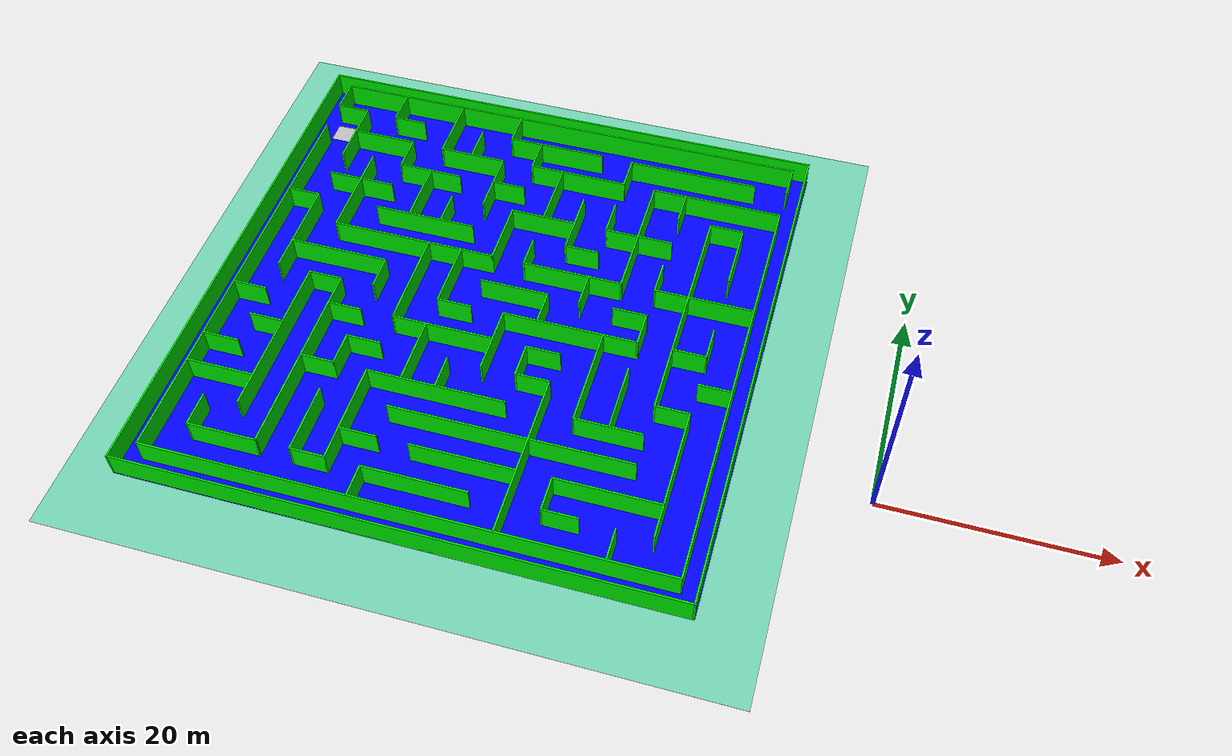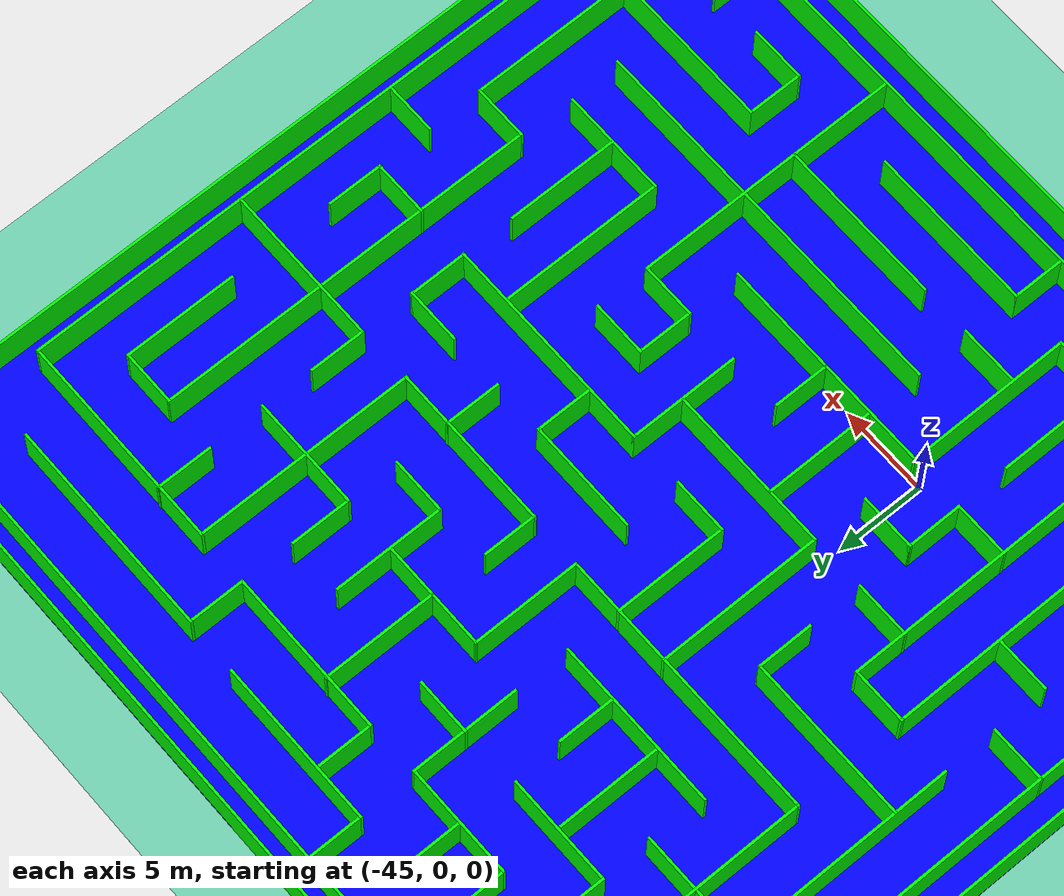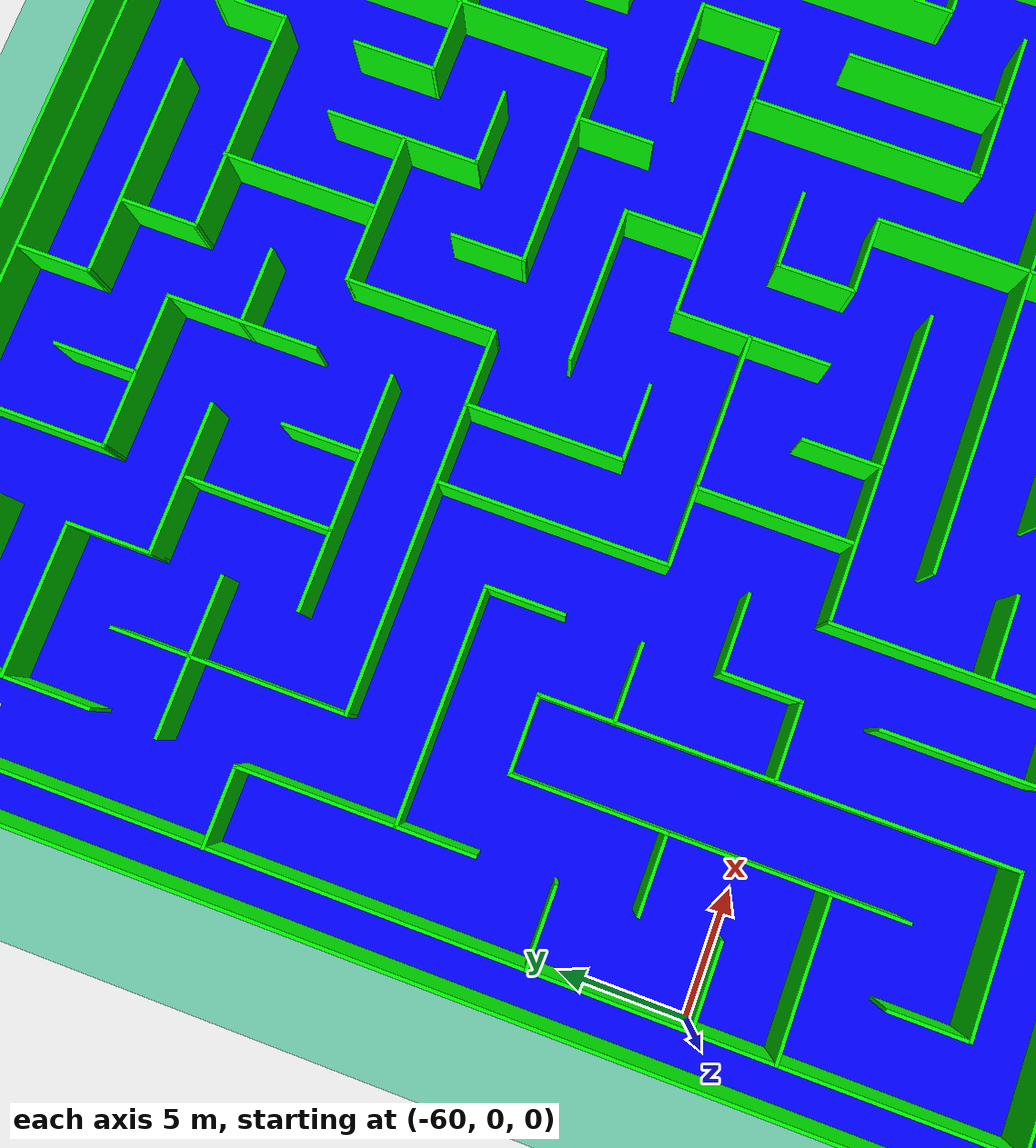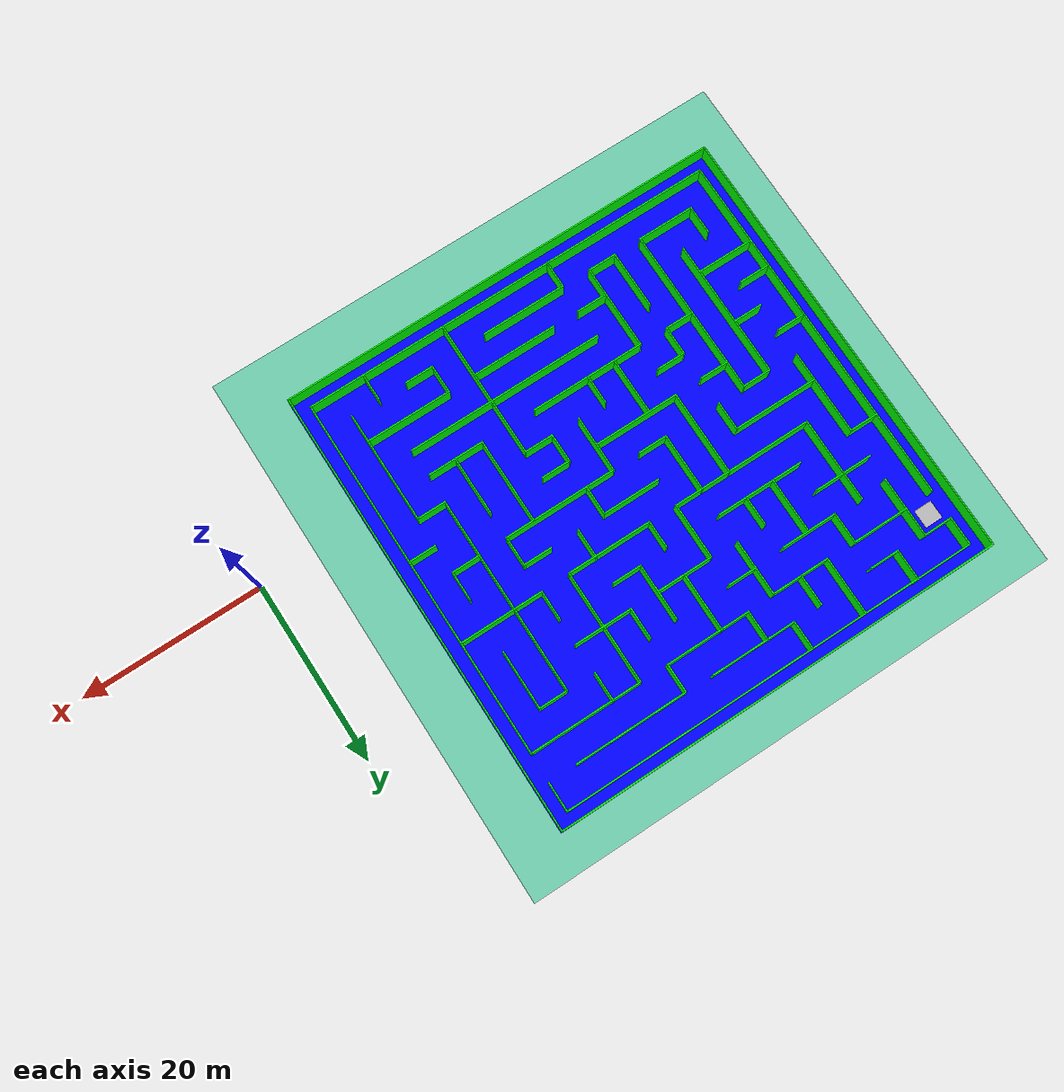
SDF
<sdf version="1.6">
 <world name="default">
  <light name="sun" type="directional">
   <pose>0 0 10 0 -0 0</pose>
   <diffuse>0.8 0.8 0.8 1</diffuse>
   <specular>0.2 0.2 0.2 1</specular>
   <attenuation>
    <range>1000</range>
    <constant>0.9</constant>
    <linear>0.01</linear>
    <quadratic>0.001</quadratic>
   </attenuation>
   <direction>-0.5 0.1 -0.9</direction>
  </light>
  <gravity>0 0 -9.8</gravity>
  <magnetic_field>6e-06 2.3e-05 -4.2e-05</magnetic_field>
  <atmosphere type="adiabatic"/>
  <physics name="default_physics" default="0" type="ode">
   <max_step_size>0.001</max_step_size>
   <real_time_factor>1</real_time_factor>
   <real_time_update_rate>1000</real_time_update_rate>
  </physics>
  <scene><ambient>0.4 0.4 0.4 1</ambient><background>0.7 0.7 0.7 1</background><shadows>1</shadows></scene>
  <audio><device>default</device></audio>
  <spherical_coordinates>
   <surface_model>EARTH_WGS84</surface_model>
   <latitude_deg>0</latitude_deg>
   <longitude_deg>0</longitude_deg>
   <elevation>0</elevation>
   <heading_deg>0</heading_deg>
  </spherical_coordinates>
  <include><uri>model://start_marker</uri><pose>-59.041698 29.635340 0.026924 0 0 -1.57</pose></include>
  <model name="Maze1">
   <pose>-36.2095 9.65499 0 0 -0 0</pose>
   <link name="Floor_0">
    <collision name="Floor_0_Collision">
     <geometry><box><size>50.0708 49.8915 0.1</size></box></geometry>
     <pose>0 0 0.05 0 -0 0</pose>
    </collision>
    <visual name="Floor_0_Visual">
     <pose>0 0 0.05 0 -0 0</pose>
     <geometry><box><size>50.0708 49.8915 0.1</size></box></geometry>
     <material>
      <script><uri>file://media/materials/scripts/gazebo.material</uri><name>Gazebo/Grey</name></script>
      <ambient>0 0 1 1</ambient>
     </material>
     <meta><layer>1</layer></meta>
    </visual>
    <pose>-0.62393 1.04415 0.001 0 -0 0</pose>
   </link>
   <link name="Wall_0">
    <collision name="Wall_0_Collision">
     <geometry><box><size>60.01 60 0.001</size></box></geometry>
     <pose>0 0 0.0005 0 -0 0</pose>
    </collision>
    <visual name="Wall_0_Visual">
     <pose>0 0 0.0005 0 -0 0</pose>
     <geometry><box><size>60.01 60 0.001</size></box></geometry>
     <material>
      <script><uri>file://media/materials/scripts/gazebo.material</uri><name>Gazebo/Grey</name></script>
      <ambient>0.435294 0.796078 0.67451 1</ambient>
     </material>
     <meta><layer>0</layer></meta>
    </visual>
    <pose>-1e-06 1e-06 0 0 -0 -1.5708</pose>
   </link>
   <link name="Wall_101">
    <collision name="Wall_101_Collision">
     <geometry><box><size>3.25 0.15 2.5</size></box></geometry>
     <pose>0 0 1.25 0 -0 0</pose>
    </collision>
    <visual name="Wall_101_Visual">
     <pose>0 0 1.25 0 -0 0</pose>
     <geometry><box><size>3.25 0.15 2.5</size></box></geometry>
     <material>
      <script><uri>file://media/materials/scripts/gazebo.material</uri><name>Gazebo/Grey</name></script>
      <ambient>0 1 0 1</ambient>
     </material>
     <meta><layer>1</layer></meta>
    </visual>
    <pose>12.0985 2.88137 0.001 0 -0 3.14159</pose>
   </link>
   <link name="Wall_103">
    <collision name="Wall_103_Collision">
     <geometry><box><size>6.5 0.15 2.5</size></box></geometry>
     <pose>0 0 1.25 0 -0 0</pose>
    </collision>
    <visual name="Wall_103_Visual">
     <pose>0 0 1.25 0 -0 0</pose>
     <geometry><box><size>6.5 0.15 2.5</size></box></geometry>
     <material>
      <script><uri>file://media/materials/scripts/gazebo.material</uri><name>Gazebo/Grey</name></script>
      <ambient>0 1 0 1</ambient>
     </material>
     <meta><layer>1</layer></meta>
    </visual>
    <pose>-5.05744 2.80401 0.001 0 -0 -1.5708</pose>
   </link>
   <link name="Wall_104">
    <collision name="Wall_104_Collision">
     <geometry><box><size>3.25 0.15 2.5</size></box></geometry>
     <pose>0 0 1.25 0 -0 0</pose>
    </collision>
    <visual name="Wall_104_Visual">
     <pose>0 0 1.25 0 -0 0</pose>
     <geometry><box><size>3.25 0.15 2.5</size></box></geometry>
     <material>
      <script><uri>file://media/materials/scripts/gazebo.material</uri><name>Gazebo/Grey</name></script>
      <ambient>0 1 0 1</ambient>
     </material>
     <meta><layer>1</layer></meta>
    </visual>
    <pose>-3.50744 -0.370993 0.001 0 -0 0</pose>
   </link>
   <link name="Wall_106">
    <collision name="Wall_106_Collision">
     <geometry><box><size>6.5 0.15 2.5</size></box></geometry>
     <pose>0 0 1.25 0 -0 0</pose>
    </collision>
    <visual name="Wall_106_Visual">
     <pose>0 0 1.25 0 -0 0</pose>
     <geometry><box><size>6.5 0.15 2.5</size></box></geometry>
     <material>
      <script><uri>file://media/materials/scripts/gazebo.material</uri><name>Gazebo/Grey</name></script>
      <ambient>0 1 0 1</ambient>
     </material>
     <meta><layer>1</layer></meta>
    </visual>
    <pose>1.17658 2.86678 0.001 0 -0 0</pose>
   </link>
   <link name="Wall_107">
    <collision name="Wall_107_Collision">
     <geometry><box><size>3.25 0.15 2.5</size></box></geometry>
     <pose>0 0 1.25 0 -0 0</pose>
    </collision>
    <visual name="Wall_107_Visual">
     <pose>0 0 1.25 0 -0 0</pose>
     <geometry><box><size>3.25 0.15 2.5</size></box></geometry>
     <material>
      <script><uri>file://media/materials/scripts/gazebo.material</uri><name>Gazebo/Grey</name></script>
      <ambient>0 1 0 1</ambient>
     </material>
     <meta><layer>1</layer></meta>
    </visual>
    <pose>4.35158 1.31678 0.001 0 -0 -1.5708</pose>
   </link>
   <link name="Wall_109">
    <collision name="Wall_109_Collision">
     <geometry><box><size>3.25 0.15 2.5</size></box></geometry>
     <pose>0 0 1.25 0 -0 0</pose>
    </collision>
    <visual name="Wall_109_Visual">
     <pose>0 0 1.25 0 -0 0</pose>
     <geometry><box><size>3.25 0.15 2.5</size></box></geometry>
     <material>
      <script><uri>file://media/materials/scripts/gazebo.material</uri><name>Gazebo/Grey</name></script>
      <ambient>0 1 0 1</ambient>
     </material>
     <meta><layer>1</layer></meta>
    </visual>
    <pose>7.36486 4.40241 0.001 0 -0 -1.5708</pose>
   </link>
   <link name="Wall_11">
    <collision name="Wall_11_Collision">
     <geometry><box><size>40.5 0.15 2.5</size></box></geometry>
     <pose>0 0 1.25 0 -0 0</pose>
    </collision>
    <visual name="Wall_11_Visual">
     <pose>0 0 1.25 0 -0 0</pose>
     <geometry><box><size>40.5 0.15 2.5</size></box></geometry>
     <material>
      <script><uri>file://media/materials/scripts/gazebo.material</uri><name>Gazebo/Grey</name></script>
      <ambient>0 1 0 1</ambient>
     </material>
     <meta><layer>1</layer></meta>
    </visual>
    <pose>-23.7929 -1.7987 0.001 0 -0 -1.5708</pose>
   </link>
   <link name="Wall_111">
    <collision name="Wall_111_Collision">
     <geometry><box><size>3 0.15 2.5</size></box></geometry>
     <pose>0 0 1.25 0 -0 0</pose>
    </collision>
    <visual name="Wall_111_Visual">
     <pose>0 0 1.25 0 -0 0</pose>
     <geometry><box><size>3 0.15 2.5</size></box></geometry>
     <material>
      <script><uri>file://media/materials/scripts/gazebo.material</uri><name>Gazebo/Grey</name></script>
      <ambient>0 1 0 1</ambient>
     </material>
     <meta><layer>1</layer></meta>
    </visual>
    <pose>-5.08108 -20.4688 0.001 0 -0 1.5708</pose>
   </link>
   <link name="Wall_112">
    <collision name="Wall_112_Collision">
     <geometry><box><size>9.5 0.15 2.5</size></box></geometry>
     <pose>0 0 1.25 0 -0 0</pose>
    </collision>
    <visual name="Wall_112_Visual">
     <pose>0 0 1.25 0 -0 0</pose>
     <geometry><box><size>9.5 0.15 2.5</size></box></geometry>
     <material>
      <script><uri>file://media/materials/scripts/gazebo.material</uri><name>Gazebo/Grey</name></script>
      <ambient>0 1 0 1</ambient>
     </material>
     <meta><layer>1</layer></meta>
    </visual>
    <pose>-0.406083 -19.0438 0.001 0 -0 0</pose>
   </link>
   <link name="Wall_114">
    <collision name="Wall_114_Collision">
     <geometry><box><size>3.5 0.15 2.5</size></box></geometry>
     <pose>0 0 1.25 0 -0 0</pose>
    </collision>
    <visual name="Wall_114_Visual">
     <pose>0 0 1.25 0 -0 0</pose>
     <geometry><box><size>3.5 0.15 2.5</size></box></geometry>
     <material>
      <script><uri>file://media/materials/scripts/gazebo.material</uri><name>Gazebo/Grey</name></script>
      <ambient>0 1 0 1</ambient>
     </material>
     <meta><layer>1</layer></meta>
    </visual>
    <pose>-6.57217 -15.9485 0.001 0 -0 0</pose>
   </link>
   <link name="Wall_116">
    <collision name="Wall_116_Collision">
     <geometry><box><size>22 0.15 2.5</size></box></geometry>
     <pose>0 0 1.25 0 -0 0</pose>
    </collision>
    <visual name="Wall_116_Visual">
     <pose>0 0 1.25 0 -0 0</pose>
     <geometry><box><size>22 0.15 2.5</size></box></geometry>
     <material>
      <script><uri>file://media/materials/scripts/gazebo.material</uri><name>Gazebo/Grey</name></script>
      <ambient>0 1 0 1</ambient>
     </material>
     <meta><layer>1</layer></meta>
    </visual>
    <pose>5.80874 -12.7473 0.001 0 -0 0</pose>
   </link>
   <link name="Wall_118">
    <collision name="Wall_118_Collision">
     <geometry><box><size>9.5 0.15 2.5</size></box></geometry>
     <pose>0 0 1.25 0 -0 0</pose>
    </collision>
    <visual name="Wall_118_Visual">
     <pose>0 0 1.25 0 -0 0</pose>
     <geometry><box><size>9.5 0.15 2.5</size></box></geometry>
     <material>
      <script><uri>file://media/materials/scripts/gazebo.material</uri><name>Gazebo/Grey</name></script>
      <ambient>0 1 0 1</ambient>
     </material>
     <meta><layer>1</layer></meta>
    </visual>
    <pose>2.68965 -15.9485 0.001 0 -0 0</pose>
   </link>
   <link name="Wall_12">
    <collision name="Wall_12_Collision">
     <geometry><box><size>46.75 0.15 2.5</size></box></geometry>
     <pose>0 0 1.25 0 -0 0</pose>
    </collision>
    <visual name="Wall_12_Visual">
     <pose>0 0 1.25 0 -0 0</pose>
     <geometry><box><size>46.75 0.15 2.5</size></box></geometry>
     <material>
      <script><uri>file://media/materials/scripts/gazebo.material</uri><name>Gazebo/Grey</name></script>
      <ambient>0 1 0 1</ambient>
     </material>
     <meta><layer>1</layer></meta>
    </visual>
    <pose>-0.4929 -21.9737 0.001 0 -0 0</pose>
   </link>
   <link name="Wall_120">
    <collision name="Wall_120_Collision">
     <geometry><box><size>15.5 0.15 2.5</size></box></geometry>
     <pose>0 0 1.25 0 -0 0</pose>
    </collision>
    <visual name="Wall_120_Visual">
     <pose>0 0 1.25 0 -0 0</pose>
     <geometry><box><size>15.5 0.15 2.5</size></box></geometry>
     <material>
      <script><uri>file://media/materials/scripts/gazebo.material</uri><name>Gazebo/Grey</name></script>
      <ambient>0 1 0 1</ambient>
     </material>
     <meta><layer>1</layer></meta>
    </visual>
    <pose>7.40738 -14.2188 0.001 0 -0 1.5708</pose>
   </link>
   <link name="Wall_121">
    <collision name="Wall_121_Collision">
     <geometry><box><size>3.25 0.15 2.5</size></box></geometry>
     <pose>0 0 1.25 0 -0 0</pose>
    </collision>
    <visual name="Wall_121_Visual">
     <pose>0 0 1.25 0 -0 0</pose>
     <geometry><box><size>3.25 0.15 2.5</size></box></geometry>
     <material>
      <script><uri>file://media/materials/scripts/gazebo.material</uri><name>Gazebo/Grey</name></script>
      <ambient>0 1 0 1</ambient>
     </material>
     <meta><layer>1</layer></meta>
    </visual>
    <pose>5.85738 -6.54376 0.001 0 -0 3.14159</pose>
   </link>
   <link name="Wall_122">
    <collision name="Wall_122_Collision">
     <geometry><box><size>3.25 0.15 2.5</size></box></geometry>
     <pose>0 0 1.25 0 -0 0</pose>
    </collision>
    <visual name="Wall_122_Visual">
     <pose>0 0 1.25 0 -0 0</pose>
     <geometry><box><size>3.25 0.15 2.5</size></box></geometry>
     <material>
      <script><uri>file://media/materials/scripts/gazebo.material</uri><name>Gazebo/Grey</name></script>
      <ambient>0 1 0 1</ambient>
     </material>
     <meta><layer>1</layer></meta>
    </visual>
    <pose>4.30738 -4.99376 0.001 0 -0 1.5708</pose>
   </link>
   <link name="Wall_125">
    <collision name="Wall_125_Collision">
     <geometry><box><size>3.25 0.15 2.5</size></box></geometry>
     <pose>0 0 1.25 0 -0 0</pose>
    </collision>
    <visual name="Wall_125_Visual">
     <pose>0 0 1.25 0 -0 0</pose>
     <geometry><box><size>3.25 0.15 2.5</size></box></geometry>
     <material>
      <script><uri>file://media/materials/scripts/gazebo.material</uri><name>Gazebo/Grey</name></script>
      <ambient>0 1 0 1</ambient>
     </material>
     <meta><layer>1</layer></meta>
    </visual>
    <pose>5.85738 -3.44376 0.001 0 -0 0</pose>
   </link>
   <link name="Wall_127">
    <collision name="Wall_127_Collision">
     <geometry><box><size>9.5 0.15 2.5</size></box></geometry>
     <pose>0 0 1.25 0 -0 0</pose>
    </collision>
    <visual name="Wall_127_Visual">
     <pose>0 0 1.25 0 -0 0</pose>
     <geometry><box><size>9.5 0.15 2.5</size></box></geometry>
     <material>
      <script><uri>file://media/materials/scripts/gazebo.material</uri><name>Gazebo/Grey</name></script>
      <ambient>0 1 0 1</ambient>
     </material>
     <meta><layer>1</layer></meta>
    </visual>
    <pose>10.4679 -5.03935 0.001 0 -0 -1.5708</pose>
   </link>
   <link name="Wall_128">
    <collision name="Wall_128_Collision">
     <geometry><box><size>6.25 0.15 2.5</size></box></geometry>
     <pose>0 0 1.25 0 -0 0</pose>
    </collision>
    <visual name="Wall_128_Visual">
     <pose>0 0 1.25 0 -0 0</pose>
     <geometry><box><size>6.25 0.15 2.5</size></box></geometry>
     <material>
      <script><uri>file://media/materials/scripts/gazebo.material</uri><name>Gazebo/Grey</name></script>
      <ambient>0 1 0 1</ambient>
     </material>
     <meta><layer>1</layer></meta>
    </visual>
    <pose>13.5179 -9.71435 0.001 0 -0 0</pose>
   </link>
   <link name="Wall_13">
    <collision name="Wall_13_Collision">
     <geometry><box><size>40.5 0.15 2.5</size></box></geometry>
     <pose>0 0 1.25 0 -0 0</pose>
    </collision>
    <visual name="Wall_13_Visual">
     <pose>0 0 1.25 0 -0 0</pose>
     <geometry><box><size>40.5 0.15 2.5</size></box></geometry>
     <material>
      <script><uri>file://media/materials/scripts/gazebo.material</uri><name>Gazebo/Grey</name></script>
      <ambient>0 1 0 1</ambient>
     </material>
     <meta><layer>1</layer></meta>
    </visual>
    <pose>22.8071 -1.7987 0.001 0 -0 1.5708</pose>
   </link>
   <link name="Wall_130">
    <collision name="Wall_130_Collision">
     <geometry><box><size>6.5 0.15 2.5</size></box></geometry>
     <pose>0 0 1.25 0 -0 0</pose>
    </collision>
    <visual name="Wall_130_Visual">
     <pose>0 0 1.25 0 -0 0</pose>
     <geometry><box><size>6.5 0.15 2.5</size></box></geometry>
     <material>
      <script><uri>file://media/materials/scripts/gazebo.material</uri><name>Gazebo/Grey</name></script>
      <ambient>0 1 0 1</ambient>
     </material>
     <meta><layer>1</layer></meta>
    </visual>
    <pose>13.5988 -6.52955 0.001 0 -0 -1.5708</pose>
   </link>
   <link name="Wall_132">
    <collision name="Wall_132_Collision">
     <geometry><box><size>3.25 0.15 2.5</size></box></geometry>
     <pose>0 0 1.25 0 -0 0</pose>
    </collision>
    <visual name="Wall_132_Visual">
     <pose>0 0 1.25 0 -0 0</pose>
     <geometry><box><size>3.25 0.15 2.5</size></box></geometry>
     <material>
      <script><uri>file://media/materials/scripts/gazebo.material</uri><name>Gazebo/Grey</name></script>
      <ambient>0 1 0 1</ambient>
     </material>
     <meta><layer>1</layer></meta>
    </visual>
    <pose>12.0179 -18.984 0.001 0 -0 3.14159</pose>
   </link>
   <link name="Wall_133">
    <collision name="Wall_133_Collision">
     <geometry><box><size>3.25 0.15 2.5</size></box></geometry>
     <pose>0 0 1.25 0 -0 0</pose>
    </collision>
    <visual name="Wall_133_Visual">
     <pose>0 0 1.25 0 -0 0</pose>
     <geometry><box><size>3.25 0.15 2.5</size></box></geometry>
     <material>
      <script><uri>file://media/materials/scripts/gazebo.material</uri><name>Gazebo/Grey</name></script>
      <ambient>0 1 0 1</ambient>
     </material>
     <meta><layer>1</layer></meta>
    </visual>
    <pose>10.4679 -17.434 0.001 0 -0 1.5708</pose>
   </link>
   <link name="Wall_134">
    <collision name="Wall_134_Collision">
     <geometry><box><size>9.5 0.15 2.5</size></box></geometry>
     <pose>0 0 1.25 0 -0 0</pose>
    </collision>
    <visual name="Wall_134_Visual">
     <pose>0 0 1.25 0 -0 0</pose>
     <geometry><box><size>9.5 0.15 2.5</size></box></geometry>
     <material>
      <script><uri>file://media/materials/scripts/gazebo.material</uri><name>Gazebo/Grey</name></script>
      <ambient>0 1 0 1</ambient>
     </material>
     <meta><layer>1</layer></meta>
    </visual>
    <pose>15.1429 -15.884 0.001 0 -0 0</pose>
   </link>
   <link name="Wall_136">
    <collision name="Wall_136_Collision">
     <geometry><box><size>3 0.15 2.5</size></box></geometry>
     <pose>0 0 1.25 0 -0 0</pose>
    </collision>
    <visual name="Wall_136_Visual">
     <pose>0 0 1.25 0 -0 0</pose>
     <geometry><box><size>3 0.15 2.5</size></box></geometry>
     <material>
      <script><uri>file://media/materials/scripts/gazebo.material</uri><name>Gazebo/Grey</name></script>
      <ambient>0 1 0 1</ambient>
     </material>
     <meta><layer>1</layer></meta>
    </visual>
    <pose>16.7235 -20.5053 0.001 0 -0 1.5708</pose>
   </link>
   <link name="Wall_138">
    <collision name="Wall_138_Collision">
     <geometry><box><size>12.5 0.15 2.5</size></box></geometry>
     <pose>0 0 1.25 0 -0 0</pose>
    </collision>
    <visual name="Wall_138_Visual">
     <pose>0 0 1.25 0 -0 0</pose>
     <geometry><box><size>12.5 0.15 2.5</size></box></geometry>
     <material>
      <script><uri>file://media/materials/scripts/gazebo.material</uri><name>Gazebo/Grey</name></script>
      <ambient>0 1 0 1</ambient>
     </material>
     <meta><layer>1</layer></meta>
    </visual>
    <pose>19.8544 -12.7651 0.001 0 -0 1.5708</pose>
   </link>
   <link name="Wall_139">
    <collision name="Wall_139_Collision">
     <geometry><box><size>3.25 0.15 2.5</size></box></geometry>
     <pose>0 0 1.25 0 -0 0</pose>
    </collision>
    <visual name="Wall_139_Visual">
     <pose>0 0 1.25 0 -0 0</pose>
     <geometry><box><size>3.25 0.15 2.5</size></box></geometry>
     <material>
      <script><uri>file://media/materials/scripts/gazebo.material</uri><name>Gazebo/Grey</name></script>
      <ambient>0 1 0 1</ambient>
     </material>
     <meta><layer>1</layer></meta>
    </visual>
    <pose>18.3044 -6.59006 0.001 0 -0 3.14159</pose>
   </link>
   <link name="Wall_14">
    <collision name="Wall_14_Collision">
     <geometry><box><size>12.5 0.15 2.5</size></box></geometry>
     <pose>0 0 1.25 0 -0 0</pose>
    </collision>
    <visual name="Wall_14_Visual">
     <pose>0 0 1.25 0 -0 0</pose>
     <geometry><box><size>12.5 0.15 2.5</size></box></geometry>
     <material>
      <script><uri>file://media/materials/scripts/gazebo.material</uri><name>Gazebo/Grey</name></script>
      <ambient>0 1 0 1</ambient>
     </material>
     <meta><layer>1</layer></meta>
    </visual>
    <pose>16.6321 18.3763 0.001 0 -0 3.14159</pose>
   </link>
   <link name="Wall_140">
    <collision name="Wall_140_Collision">
     <geometry><box><size>22 0.15 2.5</size></box></geometry>
     <pose>0 0 1.25 0 -0 0</pose>
    </collision>
    <visual name="Wall_140_Visual">
     <pose>0 0 1.25 0 -0 0</pose>
     <geometry><box><size>22 0.15 2.5</size></box></geometry>
     <material>
      <script><uri>file://media/materials/scripts/gazebo.material</uri><name>Gazebo/Grey</name></script>
      <ambient>0 1 0 1</ambient>
     </material>
     <meta><layer>1</layer></meta>
    </visual>
    <pose>16.7544 4.33494 0.001 0 -0 1.5708</pose>
   </link>
   <link name="Wall_141">
    <collision name="Wall_141_Collision">
     <geometry><box><size>3.25 0.15 2.5</size></box></geometry>
     <pose>0 0 1.25 0 -0 0</pose>
    </collision>
    <visual name="Wall_141_Visual">
     <pose>0 0 1.25 0 -0 0</pose>
     <geometry><box><size>3.25 0.15 2.5</size></box></geometry>
     <material>
      <script><uri>file://media/materials/scripts/gazebo.material</uri><name>Gazebo/Grey</name></script>
      <ambient>0 1 0 1</ambient>
     </material>
     <meta><layer>1</layer></meta>
    </visual>
    <pose>18.3044 15.2599 0.001 0 -0 0</pose>
   </link>
   <link name="Wall_142">
    <collision name="Wall_142_Collision">
     <geometry><box><size>6.5 0.15 2.5</size></box></geometry>
     <pose>0 0 1.25 0 -0 0</pose>
    </collision>
    <visual name="Wall_142_Visual">
     <pose>0 0 1.25 0 -0 0</pose>
     <geometry><box><size>6.5 0.15 2.5</size></box></geometry>
     <material>
      <script><uri>file://media/materials/scripts/gazebo.material</uri><name>Gazebo/Grey</name></script>
      <ambient>0 1 0 1</ambient>
     </material>
     <meta><layer>1</layer></meta>
    </visual>
    <pose>19.8544 12.0849 0.001 0 -0 -1.5708</pose>
   </link>
   <link name="Wall_144">
    <collision name="Wall_144_Collision">
     <geometry><box><size>3.25 0.15 2.5</size></box></geometry>
     <pose>0 0 1.25 0 -0 0</pose>
    </collision>
    <visual name="Wall_144_Visual">
     <pose>0 0 1.25 0 -0 0</pose>
     <geometry><box><size>3.25 0.15 2.5</size></box></geometry>
     <material>
      <script><uri>file://media/materials/scripts/gazebo.material</uri><name>Gazebo/Grey</name></script>
      <ambient>0 1 0 1</ambient>
     </material>
     <meta><layer>1</layer></meta>
    </visual>
    <pose>19.8424 1.28446 0.001 0 -0 -1.5708</pose>
   </link>
   <link name="Wall_145">
    <collision name="Wall_145_Collision">
     <geometry><box><size>3.25 0.15 2.5</size></box></geometry>
     <pose>0 0 1.25 0 -0 0</pose>
    </collision>
    <visual name="Wall_145_Visual">
     <pose>0 0 1.25 0 -0 0</pose>
     <geometry><box><size>3.25 0.15 2.5</size></box></geometry>
     <material>
      <script><uri>file://media/materials/scripts/gazebo.material</uri><name>Gazebo/Grey</name></script>
      <ambient>0 1 0 1</ambient>
     </material>
     <meta><layer>1</layer></meta>
    </visual>
    <pose>18.2924 -0.265535 0.001 0 -0 3.14159</pose>
   </link>
   <link name="Wall_147">
    <collision name="Wall_147_Collision">
     <geometry><box><size>3 0.15 2.5</size></box></geometry>
     <pose>0 0 1.25 0 -0 0</pose>
    </collision>
    <visual name="Wall_147_Visual">
     <pose>0 0 1.25 0 -0 0</pose>
     <geometry><box><size>3 0.15 2.5</size></box></geometry>
     <material>
      <script><uri>file://media/materials/scripts/gazebo.material</uri><name>Gazebo/Grey</name></script>
      <ambient>0 1 0 1</ambient>
     </material>
     <meta><layer>1</layer></meta>
    </visual>
    <pose>21.2876 -3.40074 0.001 0 -0 0</pose>
   </link>
   <link name="Wall_149">
    <collision name="Wall_149_Collision">
     <geometry><box><size>3.25 0.15 2.5</size></box></geometry>
     <pose>0 0 1.25 0 -0 0</pose>
    </collision>
    <visual name="Wall_149_Visual">
     <pose>0 0 1.25 0 -0 0</pose>
     <geometry><box><size>3.25 0.15 2.5</size></box></geometry>
     <material>
      <script><uri>file://media/materials/scripts/gazebo.material</uri><name>Gazebo/Grey</name></script>
      <ambient>0 1 0 1</ambient>
     </material>
     <meta><layer>1</layer></meta>
    </visual>
    <pose>13.6187 7.53453 0.001 0 -0 -1.5708</pose>
   </link>
   <link name="Wall_15">
    <collision name="Wall_15_Collision">
     <geometry><box><size>12.633 0.15 2.5</size></box></geometry>
     <pose>0 0 1.25 0 -0 0</pose>
    </collision>
    <visual name="Wall_15_Visual">
     <pose>0 0 1.25 0 -0 0</pose>
     <geometry><box><size>12.633 0.15 2.5</size></box></geometry>
     <material>
      <script><uri>file://media/materials/scripts/gazebo.material</uri><name>Gazebo/Grey</name></script>
      <ambient>0 1 0 1</ambient>
     </material>
     <meta><layer>1</layer></meta>
    </visual>
    <pose>10.4571 12.1348 0.001 0 -0 -1.5708</pose>
   </link>
   <link name="Wall_150">
    <collision name="Wall_150_Collision">
     <geometry><box><size>9.25 0.15 2.5</size></box></geometry>
     <pose>0 0 1.25 0 -0 0</pose>
    </collision>
    <visual name="Wall_150_Visual">
     <pose>0 0 1.25 0 -0 0</pose>
     <geometry><box><size>9.25 0.15 2.5</size></box></geometry>
     <material>
      <script><uri>file://media/materials/scripts/gazebo.material</uri><name>Gazebo/Grey</name></script>
      <ambient>0 1 0 1</ambient>
     </material>
     <meta><layer>1</layer></meta>
    </visual>
    <pose>18.1687 5.98453 0.001 0 -0 0</pose>
   </link>
   <link name="Wall_152">
    <collision name="Wall_152_Collision">
     <geometry><box><size>6.5 0.15 2.5</size></box></geometry>
     <pose>0 0 1.25 0 -0 0</pose>
    </collision>
    <visual name="Wall_152_Visual">
     <pose>0 0 1.25 0 -0 0</pose>
     <geometry><box><size>6.5 0.15 2.5</size></box></geometry>
     <material>
      <script><uri>file://media/materials/scripts/gazebo.material</uri><name>Gazebo/Grey</name></script>
      <ambient>0 1 0 1</ambient>
     </material>
     <meta><layer>1</layer></meta>
    </visual>
    <pose>-11.3173 21.4915 0.001 0 -0 -1.5708</pose>
   </link>
   <link name="Wall_153">
    <collision name="Wall_153_Collision">
     <geometry><box><size>6.5 0.15 2.5</size></box></geometry>
     <pose>0 0 1.25 0 -0 0</pose>
    </collision>
    <visual name="Wall_153_Visual">
     <pose>0 0 1.25 0 -0 0</pose>
     <geometry><box><size>6.5 0.15 2.5</size></box></geometry>
     <material>
      <script><uri>file://media/materials/scripts/gazebo.material</uri><name>Gazebo/Grey</name></script>
      <ambient>0 1 0 1</ambient>
     </material>
     <meta><layer>1</layer></meta>
    </visual>
    <pose>-8.14233 18.3165 0.001 0 -0 0</pose>
   </link>
   <link name="Wall_154">
    <collision name="Wall_154_Collision">
     <geometry><box><size>6.25 0.15 2.5</size></box></geometry>
     <pose>0 0 1.25 0 -0 0</pose>
    </collision>
    <visual name="Wall_154_Visual">
     <pose>0 0 1.25 0 -0 0</pose>
     <geometry><box><size>6.25 0.15 2.5</size></box></geometry>
     <material>
      <script><uri>file://media/materials/scripts/gazebo.material</uri><name>Gazebo/Grey</name></script>
      <ambient>0 1 0 1</ambient>
     </material>
     <meta><layer>1</layer></meta>
    </visual>
    <pose>-4.96733 15.2665 0.001 0 -0 -1.5708</pose>
   </link>
   <link name="Wall_156">
    <collision name="Wall_156_Collision">
     <geometry><box><size>3.25 0.15 2.5</size></box></geometry>
     <pose>0 0 1.25 0 -0 0</pose>
    </collision>
    <visual name="Wall_156_Visual">
     <pose>0 0 1.25 0 -0 0</pose>
     <geometry><box><size>3.25 0.15 2.5</size></box></geometry>
     <material>
      <script><uri>file://media/materials/scripts/gazebo.material</uri><name>Gazebo/Grey</name></script>
      <ambient>0 1 0 1</ambient>
     </material>
     <meta><layer>1</layer></meta>
    </visual>
    <pose>-3.43516 15.2753 0.001 0 -0 0</pose>
   </link>
   <link name="Wall_158">
    <collision name="Wall_158_Collision">
     <geometry><box><size>3.5 0.15 2.5</size></box></geometry>
     <pose>0 0 1.25 0 -0 0</pose>
    </collision>
    <visual name="Wall_158_Visual">
     <pose>0 0 1.25 0 -0 0</pose>
     <geometry><box><size>3.5 0.15 2.5</size></box></geometry>
     <material>
      <script><uri>file://media/materials/scripts/gazebo.material</uri><name>Gazebo/Grey</name></script>
      <ambient>0 1 0 1</ambient>
     </material>
     <meta><layer>1</layer></meta>
    </visual>
    <pose>-8.22772 19.9936 0.001 0 -0 -1.5708</pose>
   </link>
   <link name="Wall_16">
    <collision name="Wall_16_Collision">
     <geometry><box><size>9.5 0.15 2.5</size></box></geometry>
     <pose>0 0 1.25 0 -0 0</pose>
    </collision>
    <visual name="Wall_16_Visual">
     <pose>0 0 1.25 0 -0 0</pose>
     <geometry><box><size>9.5 0.15 2.5</size></box></geometry>
     <material>
      <script><uri>file://media/materials/scripts/gazebo.material</uri><name>Gazebo/Grey</name></script>
      <ambient>0 1 0 1</ambient>
     </material>
     <meta><layer>1</layer></meta>
    </visual>
    <pose>5.7821 5.9199 0.001 0 -0 3.14159</pose>
   </link>
   <link name="Wall_160">
    <collision name="Wall_160_Collision">
     <geometry><box><size>6.5 0.15 2.5</size></box></geometry>
     <pose>0 0 1.25 0 -0 0</pose>
    </collision>
    <visual name="Wall_160_Visual">
     <pose>0 0 1.25 0 -0 0</pose>
     <geometry><box><size>6.5 0.15 2.5</size></box></geometry>
     <material>
      <script><uri>file://media/materials/scripts/gazebo.material</uri><name>Gazebo/Grey</name></script>
      <ambient>0 1 0 1</ambient>
     </material>
     <meta><layer>1</layer></meta>
    </visual>
    <pose>1.16348 15.2995 0.001 0 -0 1.5708</pose>
   </link>
   <link name="Wall_164">
    <collision name="Wall_164_Collision">
     <geometry><box><size>6.37236 0.15 2.5</size></box></geometry>
     <pose>0 0 1.25 0 -0 0</pose>
    </collision>
    <visual name="Wall_164_Visual">
     <pose>0 0 1.25 0 -0 0</pose>
     <geometry><box><size>6.37236 0.15 2.5</size></box></geometry>
     <material>
      <script><uri>file://media/materials/scripts/gazebo.material</uri><name>Gazebo/Grey</name></script>
      <ambient>0 1 0 1</ambient>
     </material>
     <meta><layer>1</layer></meta>
    </visual>
    <pose>4.2225 12.1641 0.001 0 -0 -1.5708</pose>
   </link>
   <link name="Wall_165">
    <collision name="Wall_165_Collision">
     <geometry><box><size>3.25 0.15 2.5</size></box></geometry>
     <pose>0 0 1.25 0 -0 0</pose>
    </collision>
    <visual name="Wall_165_Visual">
     <pose>0 0 1.25 0 -0 0</pose>
     <geometry><box><size>3.25 0.15 2.5</size></box></geometry>
     <material>
      <script><uri>file://media/materials/scripts/gazebo.material</uri><name>Gazebo/Grey</name></script>
      <ambient>0 1 0 1</ambient>
     </material>
     <meta><layer>1</layer></meta>
    </visual>
    <pose>5.80309 9.05292 0.001 0 -0 0</pose>
   </link>
   <link name="Wall_167">
    <collision name="Wall_167_Collision">
     <geometry><box><size>6.25 0.15 2.5</size></box></geometry>
     <pose>0 0 1.25 0 -0 0</pose>
    </collision>
    <visual name="Wall_167_Visual">
     <pose>0 0 1.25 0 -0 0</pose>
     <geometry><box><size>6.25 0.15 2.5</size></box></geometry>
     <material>
      <script><uri>file://media/materials/scripts/gazebo.material</uri><name>Gazebo/Grey</name></script>
      <ambient>0 1 0 1</ambient>
     </material>
     <meta><layer>1</layer></meta>
    </visual>
    <pose>1.06978 12.0785 0.001 0 -0 0</pose>
   </link>
   <link name="Wall_169">
    <collision name="Wall_169_Collision">
     <geometry><box><size>3.5 0.15 2.5</size></box></geometry>
     <pose>0 0 1.25 0 -0 0</pose>
    </collision>
    <visual name="Wall_169_Visual">
     <pose>0 0 1.25 0 -0 0</pose>
     <geometry><box><size>3.5 0.15 2.5</size></box></geometry>
     <material>
      <script><uri>file://media/materials/scripts/gazebo.material</uri><name>Gazebo/Grey</name></script>
      <ambient>0 1 0 1</ambient>
     </material>
     <meta><layer>1</layer></meta>
    </visual>
    <pose>7.34271 13.7226 0.001 0 -0 -1.5708</pose>
   </link>
   <link name="Wall_17">
    <collision name="Wall_17_Collision">
     <geometry><box><size>3.133 0.15 2.5</size></box></geometry>
     <pose>0 0 1.25 0 -0 0</pose>
    </collision>
    <visual name="Wall_17_Visual">
     <pose>0 0 1.25 0 -0 0</pose>
     <geometry><box><size>3.133 0.15 2.5</size></box></geometry>
     <material>
      <script><uri>file://media/materials/scripts/gazebo.material</uri><name>Gazebo/Grey</name></script>
      <ambient>0 1 0 1</ambient>
     </material>
     <meta><layer>1</layer></meta>
    </visual>
    <pose>1.1071 7.3848 0.001 0 -0 1.5708</pose>
   </link>
   <link name="Wall_170">
    <collision name="Wall_170_Collision">
     <geometry><box><size>6.5 0.15 2.5</size></box></geometry>
     <pose>0 0 1.25 0 -0 0</pose>
    </collision>
    <visual name="Wall_170_Visual">
     <pose>0 0 1.25 0 -0 0</pose>
     <geometry><box><size>6.5 0.15 2.5</size></box></geometry>
     <material>
      <script><uri>file://media/materials/scripts/gazebo.material</uri><name>Gazebo/Grey</name></script>
      <ambient>0 1 0 1</ambient>
     </material>
     <meta><layer>1</layer></meta>
    </visual>
    <pose>10.5177 12.0476 0.001 0 -0 0</pose>
   </link>
   <link name="Wall_172">
    <collision name="Wall_172_Collision">
     <geometry><box><size>3.25 0.15 2.5</size></box></geometry>
     <pose>0 0 1.25 0 -0 0</pose>
    </collision>
    <visual name="Wall_172_Visual">
     <pose>0 0 1.25 0 -0 0</pose>
     <geometry><box><size>3.25 0.15 2.5</size></box></geometry>
     <material>
      <script><uri>file://media/materials/scripts/gazebo.material</uri><name>Gazebo/Grey</name></script>
      <ambient>0 1 0 1</ambient>
     </material>
     <meta><layer>1</layer></meta>
    </visual>
    <pose>13.6137 16.8761 0.001 0 -0 -1.5708</pose>
   </link>
   <link name="Wall_174">
    <collision name="Wall_174_Collision">
     <geometry><box><size>12.5 0.15 2.5</size></box></geometry>
     <pose>0 0 1.25 0 -0 0</pose>
    </collision>
    <visual name="Wall_174_Visual">
     <pose>0 0 1.25 0 -0 0</pose>
     <geometry><box><size>12.5 0.15 2.5</size></box></geometry>
     <material>
      <script><uri>file://media/materials/scripts/gazebo.material</uri><name>Gazebo/Grey</name></script>
      <ambient>0 1 0 1</ambient>
     </material>
     <meta><layer>1</layer></meta>
    </visual>
    <pose>13.5567 21.5157 0.001 0 -0 3.14159</pose>
   </link>
   <link name="Wall_175">
    <collision name="Wall_175_Collision">
     <geometry><box><size>3.25 0.15 2.5</size></box></geometry>
     <pose>0 0 1.25 0 -0 0</pose>
    </collision>
    <visual name="Wall_175_Visual">
     <pose>0 0 1.25 0 -0 0</pose>
     <geometry><box><size>3.25 0.15 2.5</size></box></geometry>
     <material>
      <script><uri>file://media/materials/scripts/gazebo.material</uri><name>Gazebo/Grey</name></script>
      <ambient>0 1 0 1</ambient>
     </material>
     <meta><layer>1</layer></meta>
    </visual>
    <pose>7.38175 19.9657 0.001 0 -0 -1.5708</pose>
   </link>
   <link name="Wall_176">
    <collision name="Wall_176_Collision">
     <geometry><box><size>9.5 0.15 2.5</size></box></geometry>
     <pose>0 0 1.25 0 -0 0</pose>
    </collision>
    <visual name="Wall_176_Visual">
     <pose>0 0 1.25 0 -0 0</pose>
     <geometry><box><size>9.5 0.15 2.5</size></box></geometry>
     <material>
      <script><uri>file://media/materials/scripts/gazebo.material</uri><name>Gazebo/Grey</name></script>
      <ambient>0 1 0 1</ambient>
     </material>
     <meta><layer>1</layer></meta>
    </visual>
    <pose>2.70675 18.4157 0.001 0 -0 3.14159</pose>
   </link>
   <link name="Wall_177">
    <collision name="Wall_177_Collision">
     <geometry><box><size>3.25 0.15 2.5</size></box></geometry>
     <pose>0 0 1.25 0 -0 0</pose>
    </collision>
    <visual name="Wall_177_Visual">
     <pose>0 0 1.25 0 -0 0</pose>
     <geometry><box><size>3.25 0.15 2.5</size></box></geometry>
     <material>
      <script><uri>file://media/materials/scripts/gazebo.material</uri><name>Gazebo/Grey</name></script>
      <ambient>0 1 0 1</ambient>
     </material>
     <meta><layer>1</layer></meta>
    </visual>
    <pose>-1.96825 19.9657 0.001 0 -0 1.5708</pose>
   </link>
   <link name="Wall_181">
    <collision name="Wall_181_Collision">
     <geometry><box><size>9.5 0.15 2.5</size></box></geometry>
     <pose>0 0 1.25 0 -0 0</pose>
    </collision>
    <visual name="Wall_181_Visual">
     <pose>0 0 1.25 0 -0 0</pose>
     <geometry><box><size>9.5 0.15 2.5</size></box></geometry>
     <material>
      <script><uri>file://media/materials/scripts/gazebo.material</uri><name>Gazebo/Grey</name></script>
      <ambient>0 1 0 1</ambient>
     </material>
     <meta><layer>1</layer></meta>
    </visual>
    <pose>-0.421907 21.6075 0.001 0 -0 3.14159</pose>
   </link>
   <link name="Wall_182">
    <collision name="Wall_182_Collision">
     <geometry><box><size>3.25 0.15 2.5</size></box></geometry>
     <pose>0 0 1.25 0 -0 0</pose>
    </collision>
    <visual name="Wall_182_Visual">
     <pose>0 0 1.25 0 -0 0</pose>
     <geometry><box><size>3.25 0.15 2.5</size></box></geometry>
     <material>
      <script><uri>file://media/materials/scripts/gazebo.material</uri><name>Gazebo/Grey</name></script>
      <ambient>0 1 0 1</ambient>
     </material>
     <meta><layer>1</layer></meta>
    </visual>
    <pose>-5.09691 23.1575 0.001 0 -0 1.5708</pose>
   </link>
   <link name="Wall_184">
    <collision name="Wall_184_Collision">
     <geometry><box><size>49.8916 0.15 2.5</size></box></geometry>
     <pose>0 0 1.25 0 -0 0</pose>
    </collision>
    <visual name="Wall_184_Visual">
     <pose>0 0 1.25 0 -0 0</pose>
     <geometry><box><size>49.8916 0.15 2.5</size></box></geometry>
     <material>
      <script><uri>file://media/materials/scripts/gazebo.material</uri><name>Gazebo/Grey</name></script>
      <ambient>0 1 0 1</ambient>
     </material>
     <meta><layer>1</layer></meta>
    </visual>
    <pose>-25.5843 1.04415 0.001 0 -0 -1.5708</pose>
   </link>
   <link name="Wall_185">
    <collision name="Wall_185_Collision">
     <geometry><box><size>50 0.15 2.5</size></box></geometry>
     <pose>0 0 1.25 0 -0 0</pose>
    </collision>
    <visual name="Wall_185_Visual">
     <pose>0 0 1.25 0 -0 0</pose>
     <geometry><box><size>50 0.15 2.5</size></box></geometry>
     <material>
      <script><uri>file://media/materials/scripts/gazebo.material</uri><name>Gazebo/Grey</name></script>
      <ambient>0 1 0 1</ambient>
     </material>
     <meta><layer>1</layer></meta>
    </visual>
    <pose>-0.588552 -23.8266 0.001 0 -0 0</pose>
   </link>
   <link name="Wall_186">
    <collision name="Wall_186_Collision">
     <geometry><box><size>49.8916 0.15 2.5</size></box></geometry>
     <pose>0 0 1.25 0 -0 0</pose>
    </collision>
    <visual name="Wall_186_Visual">
     <pose>0 0 1.25 0 -0 0</pose>
     <geometry><box><size>49.8916 0.15 2.5</size></box></geometry>
     <material>
      <script><uri>file://media/materials/scripts/gazebo.material</uri><name>Gazebo/Grey</name></script>
      <ambient>0 1 0 1</ambient>
     </material>
     <meta><layer>1</layer></meta>
    </visual>
    <pose>24.2657 1.04415 0.001 0 -0 1.5708</pose>
   </link>
   <link name="Wall_187">
    <collision name="Wall_187_Collision">
     <geometry><box><size>50 0.15 2.5</size></box></geometry>
     <pose>0 0 1.25 0 -0 0</pose>
    </collision>
    <visual name="Wall_187_Visual">
     <pose>0 0 1.25 0 -0 0</pose>
     <geometry><box><size>50 0.15 2.5</size></box></geometry>
     <material>
      <script><uri>file://media/materials/scripts/gazebo.material</uri><name>Gazebo/Grey</name></script>
      <ambient>0 1 0 1</ambient>
     </material>
     <meta><layer>1</layer></meta>
    </visual>
    <pose>-0.659309 25.9149 0.001 0 -0 3.14159</pose>
   </link>
   <link name="Wall_19">
    <collision name="Wall_19_Collision">
     <geometry><box><size>3.5 0.15 2.5</size></box></geometry>
     <pose>0 0 1.25 0 -0 0</pose>
    </collision>
    <visual name="Wall_19_Visual">
     <pose>0 0 1.25 0 -0 0</pose>
     <geometry><box><size>3.5 0.15 2.5</size></box></geometry>
     <material>
      <script><uri>file://media/materials/scripts/gazebo.material</uri><name>Gazebo/Grey</name></script>
      <ambient>0 1 0 1</ambient>
     </material>
     <meta><layer>1</layer></meta>
    </visual>
    <pose>-17.4955 23.0694 0.001 0 -0 -1.5708</pose>
   </link>
   <link name="Wall_2">
    <collision name="Wall_2_Collision">
     <geometry><box><size>0.159962 0.15 0.001</size></box></geometry>
     <pose>0 0 0.0005 0 -0 0</pose>
    </collision>
    <visual name="Wall_2_Visual">
     <pose>0 0 0.0005 0 -0 0</pose>
     <geometry><box><size>0.159962 0.15 0.001</size></box></geometry>
     <material>
      <script><uri>file://media/materials/scripts/gazebo.material</uri><name>Gazebo/Grey</name></script>
      <ambient>0.435294 0.796078 0.67451 1</ambient>
     </material>
     <meta><layer>1</layer></meta>
    </visual>
    <pose>-0.650993 1.05733 0.001 0 -0 -1.5708</pose>
   </link>
   <link name="Wall_22">
    <collision name="Wall_22_Collision">
     <geometry><box><size>3.25 0.15 2.5</size></box></geometry>
     <pose>0 0 1.25 0 -0 0</pose>
    </collision>
    <visual name="Wall_22_Visual">
     <pose>0 0 1.25 0 -0 0</pose>
     <geometry><box><size>3.25 0.15 2.5</size></box></geometry>
     <material>
      <script><uri>file://media/materials/scripts/gazebo.material</uri><name>Gazebo/Grey</name></script>
      <ambient>0 1 0 1</ambient>
     </material>
     <meta><layer>1</layer></meta>
    </visual>
    <pose>-15.9455 21.3944 0.001 0 -0 0</pose>
   </link>
   <link name="Wall_24">
    <collision name="Wall_24_Collision">
     <geometry><box><size>6.25 0.15 2.5</size></box></geometry>
     <pose>0 0 1.25 0 -0 0</pose>
    </collision>
    <visual name="Wall_24_Visual">
     <pose>0 0 1.25 0 -0 0</pose>
     <geometry><box><size>6.25 0.15 2.5</size></box></geometry>
     <material>
      <script><uri>file://media/materials/scripts/gazebo.material</uri><name>Gazebo/Grey</name></script>
      <ambient>0 1 0 1</ambient>
     </material>
     <meta><layer>1</layer></meta>
    </visual>
    <pose>-17.5543 18.4456 0.001 0 -0 0</pose>
   </link>
   <link name="Wall_25">
    <collision name="Wall_25_Collision">
     <geometry><box><size>3.5 0.15 2.5</size></box></geometry>
     <pose>0 0 1.25 0 -0 0</pose>
    </collision>
    <visual name="Wall_25_Visual">
     <pose>0 0 1.25 0 -0 0</pose>
     <geometry><box><size>3.5 0.15 2.5</size></box></geometry>
     <material>
      <script><uri>file://media/materials/scripts/gazebo.material</uri><name>Gazebo/Grey</name></script>
      <ambient>0 1 0 1</ambient>
     </material>
     <meta><layer>1</layer></meta>
    </visual>
    <pose>-14.5043 16.7706 0.001 0 -0 -1.5708</pose>
   </link>
   <link name="Wall_26">
    <collision name="Wall_26_Collision">
     <geometry><box><size>6.25 0.15 2.5</size></box></geometry>
     <pose>0 0 1.25 0 -0 0</pose>
    </collision>
    <visual name="Wall_26_Visual">
     <pose>0 0 1.25 0 -0 0</pose>
     <geometry><box><size>6.25 0.15 2.5</size></box></geometry>
     <material>
      <script><uri>file://media/materials/scripts/gazebo.material</uri><name>Gazebo/Grey</name></script>
      <ambient>0 1 0 1</ambient>
     </material>
     <meta><layer>1</layer></meta>
    </visual>
    <pose>-11.4543 15.0956 0.001 0 -0 0</pose>
   </link>
   <link name="Wall_28">
    <collision name="Wall_28_Collision">
     <geometry><box><size>6 0.15 2.5</size></box></geometry>
     <pose>0 0 1.25 0 -0 0</pose>
    </collision>
    <visual name="Wall_28_Visual">
     <pose>0 0 1.25 0 -0 0</pose>
     <geometry><box><size>6 0.15 2.5</size></box></geometry>
     <material>
      <script><uri>file://media/materials/scripts/gazebo.material</uri><name>Gazebo/Grey</name></script>
      <ambient>0 1 0 1</ambient>
     </material>
     <meta><layer>1</layer></meta>
    </visual>
    <pose>-11.346 11.9848 0.001 0 -0 -1.5708</pose>
   </link>
   <link name="Wall_3">
    <collision name="Wall_3_Collision">
     <geometry><box><size>46.75 0.15 2.5</size></box></geometry>
     <pose>0 0 1.25 0 -0 0</pose>
    </collision>
    <visual name="Wall_3_Visual">
     <pose>0 0 1.25 0 -0 0</pose>
     <geometry><box><size>46.75 0.15 2.5</size></box></geometry>
     <material>
      <script><uri>file://media/materials/scripts/gazebo.material</uri><name>Gazebo/Grey</name></script>
      <ambient>0 1 0 1</ambient>
     </material>
     <meta><layer>1</layer></meta>
    </visual>
    <pose>-0.422143 24.6737 0.001 0 -0 0</pose>
   </link>
   <link name="Wall_31">
    <collision name="Wall_31_Collision">
     <geometry><box><size>9.75 0.15 2.5</size></box></geometry>
     <pose>0 0 1.25 0 -0 0</pose>
    </collision>
    <visual name="Wall_31_Visual">
     <pose>0 0 1.25 0 -0 0</pose>
     <geometry><box><size>9.75 0.15 2.5</size></box></geometry>
     <material>
      <script><uri>file://media/materials/scripts/gazebo.material</uri><name>Gazebo/Grey</name></script>
      <ambient>0 1 0 1</ambient>
     </material>
     <meta><layer>1</layer></meta>
    </visual>
    <pose>-9.80268 9.0478 0.001 0 -0 0</pose>
   </link>
   <link name="Wall_33">
    <collision name="Wall_33_Collision">
     <geometry><box><size>6.5 0.15 2.5</size></box></geometry>
     <pose>0 0 1.25 0 -0 0</pose>
    </collision>
    <visual name="Wall_33_Visual">
     <pose>0 0 1.25 0 -0 0</pose>
     <geometry><box><size>6.5 0.15 2.5</size></box></geometry>
     <material>
      <script><uri>file://media/materials/scripts/gazebo.material</uri><name>Gazebo/Grey</name></script>
      <ambient>0 1 0 1</ambient>
     </material>
     <meta><layer>1</layer></meta>
    </visual>
    <pose>-17.5688 12.2114 0.001 0 -0 0</pose>
   </link>
   <link name="Wall_35">
    <collision name="Wall_35_Collision">
     <geometry><box><size>9.5 0.15 2.5</size></box></geometry>
     <pose>0 0 1.25 0 -0 0</pose>
    </collision>
    <visual name="Wall_35_Visual">
     <pose>0 0 1.25 0 -0 0</pose>
     <geometry><box><size>9.5 0.15 2.5</size></box></geometry>
     <material>
      <script><uri>file://media/materials/scripts/gazebo.material</uri><name>Gazebo/Grey</name></script>
      <ambient>0 1 0 1</ambient>
     </material>
     <meta><layer>1</layer></meta>
    </visual>
    <pose>-17.5802 10.6535 0.001 0 -0 -1.5708</pose>
   </link>
   <link name="Wall_36">
    <collision name="Wall_36_Collision">
     <geometry><box><size>15.75 0.15 2.5</size></box></geometry>
     <pose>0 0 1.25 0 -0 0</pose>
    </collision>
    <visual name="Wall_36_Visual">
     <pose>0 0 1.25 0 -0 0</pose>
     <geometry><box><size>15.75 0.15 2.5</size></box></geometry>
     <material>
      <script><uri>file://media/materials/scripts/gazebo.material</uri><name>Gazebo/Grey</name></script>
      <ambient>0 1 0 1</ambient>
     </material>
     <meta><layer>1</layer></meta>
    </visual>
    <pose>-9.78021 5.97853 0.001 0 -0 0</pose>
   </link>
   <link name="Wall_37">
    <collision name="Wall_37_Collision">
     <geometry><box><size>6.25 0.15 2.5</size></box></geometry>
     <pose>0 0 1.25 0 -0 0</pose>
    </collision>
    <visual name="Wall_37_Visual">
     <pose>0 0 1.25 0 -0 0</pose>
     <geometry><box><size>6.25 0.15 2.5</size></box></geometry>
     <material>
      <script><uri>file://media/materials/scripts/gazebo.material</uri><name>Gazebo/Grey</name></script>
      <ambient>0 1 0 1</ambient>
     </material>
     <meta><layer>1</layer></meta>
    </visual>
    <pose>-1.98021 9.02853 0.001 0 -0 1.5708</pose>
   </link>
   <link name="Wall_42">
    <collision name="Wall_42_Collision">
     <geometry><box><size>3.25 0.15 2.5</size></box></geometry>
     <pose>0 0 1.25 0 -0 0</pose>
    </collision>
    <visual name="Wall_42_Visual">
     <pose>0 0 1.25 0 -0 0</pose>
     <geometry><box><size>3.25 0.15 2.5</size></box></geometry>
     <material>
      <script><uri>file://media/materials/scripts/gazebo.material</uri><name>Gazebo/Grey</name></script>
      <ambient>0 1 0 1</ambient>
     </material>
     <meta><layer>1</layer></meta>
    </visual>
    <pose>-8.18238 10.708 0.001 0 -0 -1.5708</pose>
   </link>
   <link name="Wall_44">
    <collision name="Wall_44_Collision">
     <geometry><box><size>3.25 0.15 2.5</size></box></geometry>
     <pose>0 0 1.25 0 -0 0</pose>
    </collision>
    <visual name="Wall_44_Visual">
     <pose>0 0 1.25 0 -0 0</pose>
     <geometry><box><size>3.25 0.15 2.5</size></box></geometry>
     <material>
      <script><uri>file://media/materials/scripts/gazebo.material</uri><name>Gazebo/Grey</name></script>
      <ambient>0 1 0 1</ambient>
     </material>
     <meta><layer>1</layer></meta>
    </visual>
    <pose>-22.2644 9.09432 0.001 0 -0 0</pose>
   </link>
   <link name="Wall_45">
    <collision name="Wall_45_Collision">
     <geometry><box><size>9.5 0.15 2.5</size></box></geometry>
     <pose>0 0 1.25 0 -0 0</pose>
    </collision>
    <visual name="Wall_45_Visual">
     <pose>0 0 1.25 0 -0 0</pose>
     <geometry><box><size>9.5 0.15 2.5</size></box></geometry>
     <material>
      <script><uri>file://media/materials/scripts/gazebo.material</uri><name>Gazebo/Grey</name></script>
      <ambient>0 1 0 1</ambient>
     </material>
     <meta><layer>1</layer></meta>
    </visual>
    <pose>-20.7144 4.41932 0.001 0 -0 -1.5708</pose>
   </link>
   <link name="Wall_47">
    <collision name="Wall_47_Collision">
     <geometry><box><size>9.5 0.15 2.5</size></box></geometry>
     <pose>0 0 1.25 0 -0 0</pose>
    </collision>
    <visual name="Wall_47_Visual">
     <pose>0 0 1.25 0 -0 0</pose>
     <geometry><box><size>9.5 0.15 2.5</size></box></geometry>
     <material>
      <script><uri>file://media/materials/scripts/gazebo.material</uri><name>Gazebo/Grey</name></script>
      <ambient>0 1 0 1</ambient>
     </material>
     <meta><layer>1</layer></meta>
    </visual>
    <pose>-16.0223 2.8136 0.001 0 -0 0</pose>
   </link>
   <link name="Wall_48">
    <collision name="Wall_48_Collision">
     <geometry><box><size>3.25 0.15 2.5</size></box></geometry>
     <pose>0 0 1.25 0 -0 0</pose>
    </collision>
    <visual name="Wall_48_Visual">
     <pose>0 0 1.25 0 -0 0</pose>
     <geometry><box><size>3.25 0.15 2.5</size></box></geometry>
     <material>
      <script><uri>file://media/materials/scripts/gazebo.material</uri><name>Gazebo/Grey</name></script>
      <ambient>0 1 0 1</ambient>
     </material>
     <meta><layer>1</layer></meta>
    </visual>
    <pose>-11.3473 1.2636 0.001 0 -0 -1.5708</pose>
   </link>
   <link name="Wall_5">
    <collision name="Wall_5_Collision">
     <geometry><box><size>3.25 0.15 2.5</size></box></geometry>
     <pose>0 0 1.25 0 -0 0</pose>
    </collision>
    <visual name="Wall_5_Visual">
     <pose>0 0 1.25 0 -0 0</pose>
     <geometry><box><size>3.25 0.15 2.5</size></box></geometry>
     <material>
      <script><uri>file://media/materials/scripts/gazebo.material</uri><name>Gazebo/Grey</name></script>
      <ambient>0 1 0 1</ambient>
     </material>
     <meta><layer>1</layer></meta>
    </visual>
    <pose>-23.7221 23.1237 0.001 0 -0 -1.5708</pose>
   </link>
   <link name="Wall_50">
    <collision name="Wall_50_Collision">
     <geometry><box><size>3.25 0.15 2.5</size></box></geometry>
     <pose>0 0 1.25 0 -0 0</pose>
    </collision>
    <visual name="Wall_50_Visual">
     <pose>0 0 1.25 0 -0 0</pose>
     <geometry><box><size>3.25 0.15 2.5</size></box></geometry>
     <material>
      <script><uri>file://media/materials/scripts/gazebo.material</uri><name>Gazebo/Grey</name></script>
      <ambient>0 1 0 1</ambient>
     </material>
     <meta><layer>1</layer></meta>
    </visual>
    <pose>-22.2451 -3.36882 0.001 0 -0 0</pose>
   </link>
   <link name="Wall_52">
    <collision name="Wall_52_Collision">
     <geometry><box><size>3.25 0.15 2.5</size></box></geometry>
     <pose>0 0 1.25 0 -0 0</pose>
    </collision>
    <visual name="Wall_52_Visual">
     <pose>0 0 1.25 0 -0 0</pose>
     <geometry><box><size>3.25 0.15 2.5</size></box></geometry>
     <material>
      <script><uri>file://media/materials/scripts/gazebo.material</uri><name>Gazebo/Grey</name></script>
      <ambient>0 1 0 1</ambient>
     </material>
     <meta><layer>1</layer></meta>
    </visual>
    <pose>-19.0943 -6.51961 0.001 0 -0 0</pose>
   </link>
   <link name="Wall_54">
    <collision name="Wall_54_Collision">
     <geometry><box><size>3.25 0.15 2.5</size></box></geometry>
     <pose>0 0 1.25 0 -0 0</pose>
    </collision>
    <visual name="Wall_54_Visual">
     <pose>0 0 1.25 0 -0 0</pose>
     <geometry><box><size>3.25 0.15 2.5</size></box></geometry>
     <material>
      <script><uri>file://media/materials/scripts/gazebo.material</uri><name>Gazebo/Grey</name></script>
      <ambient>0 1 0 1</ambient>
     </material>
     <meta><layer>1</layer></meta>
    </visual>
    <pose>-15.9943 -0.419613 0.001 0 -0 0</pose>
   </link>
   <link name="Wall_55">
    <collision name="Wall_55_Collision">
     <geometry><box><size>18.75 0.15 2.5</size></box></geometry>
     <pose>0 0 1.25 0 -0 0</pose>
    </collision>
    <visual name="Wall_55_Visual">
     <pose>0 0 1.25 0 -0 0</pose>
     <geometry><box><size>18.75 0.15 2.5</size></box></geometry>
     <material>
      <script><uri>file://media/materials/scripts/gazebo.material</uri><name>Gazebo/Grey</name></script>
      <ambient>0 1 0 1</ambient>
     </material>
     <meta><layer>1</layer></meta>
    </visual>
    <pose>-14.4443 -9.71961 0.001 0 -0 -1.5708</pose>
   </link>
   <link name="Wall_56">
    <collision name="Wall_56_Collision">
     <geometry><box><size>6.35928 0.15 2.5</size></box></geometry>
     <pose>0 0 1.25 0 -0 0</pose>
    </collision>
    <visual name="Wall_56_Visual">
     <pose>0 0 1.25 0 -0 0</pose>
     <geometry><box><size>6.35928 0.15 2.5</size></box></geometry>
     <material>
      <script><uri>file://media/materials/scripts/gazebo.material</uri><name>Gazebo/Grey</name></script>
      <ambient>0 1 0 1</ambient>
     </material>
     <meta><layer>1</layer></meta>
    </visual>
    <pose>-17.5489 -19.0196 0.001 0 -0 3.14159</pose>
   </link>
   <link name="Wall_57">
    <collision name="Wall_57_Collision">
     <geometry><box><size>3.25 0.15 2.5</size></box></geometry>
     <pose>0 0 1.25 0 -0 0</pose>
    </collision>
    <visual name="Wall_57_Visual">
     <pose>0 0 1.25 0 -0 0</pose>
     <geometry><box><size>3.25 0.15 2.5</size></box></geometry>
     <material>
      <script><uri>file://media/materials/scripts/gazebo.material</uri><name>Gazebo/Grey</name></script>
      <ambient>0 1 0 1</ambient>
     </material>
     <meta><layer>1</layer></meta>
    </visual>
    <pose>-20.6888 -17.4696 0.001 0 -0 1.5708</pose>
   </link>
   <link name="Wall_59">
    <collision name="Wall_59_Collision">
     <geometry><box><size>3.5 0.15 2.5</size></box></geometry>
     <pose>0 0 1.25 0 -0 0</pose>
    </collision>
    <visual name="Wall_59_Visual">
     <pose>0 0 1.25 0 -0 0</pose>
     <geometry><box><size>3.5 0.15 2.5</size></box></geometry>
     <material>
      <script><uri>file://media/materials/scripts/gazebo.material</uri><name>Gazebo/Grey</name></script>
      <ambient>0 1 0 1</ambient>
     </material>
     <meta><layer>1</layer></meta>
    </visual>
    <pose>-22.1467 -9.62055 0.001 0 -0 0</pose>
   </link>
   <link name="Wall_6">
    <collision name="Wall_6_Collision">
     <geometry><box><size>3.25 0.15 2.5</size></box></geometry>
     <pose>0 0 1.25 0 -0 0</pose>
    </collision>
    <visual name="Wall_6_Visual">
     <pose>0 0 1.25 0 -0 0</pose>
     <geometry><box><size>3.25 0.15 2.5</size></box></geometry>
     <material>
      <script><uri>file://media/materials/scripts/gazebo.material</uri><name>Gazebo/Grey</name></script>
      <ambient>0 1 0 1</ambient>
     </material>
     <meta><layer>1</layer></meta>
    </visual>
    <pose>-22.1721 21.5737 0.001 0 -0 0</pose>
   </link>
   <link name="Wall_65">
    <collision name="Wall_65_Collision">
     <geometry><box><size>15.5 0.15 2.5</size></box></geometry>
     <pose>0 0 1.25 0 -0 0</pose>
    </collision>
    <visual name="Wall_65_Visual">
     <pose>0 0 1.25 0 -0 0</pose>
     <geometry><box><size>15.5 0.15 2.5</size></box></geometry>
     <material>
      <script><uri>file://media/materials/scripts/gazebo.material</uri><name>Gazebo/Grey</name></script>
      <ambient>0 1 0 1</ambient>
     </material>
     <meta><layer>1</layer></meta>
    </visual>
    <pose>-17.5443 -8.09461 0.001 0 -0 -1.5708</pose>
   </link>
   <link name="Wall_67">
    <collision name="Wall_67_Collision">
     <geometry><box><size>6.25 0.15 2.5</size></box></geometry>
     <pose>0 0 1.25 0 -0 0</pose>
    </collision>
    <visual name="Wall_67_Visual">
     <pose>0 0 1.25 0 -0 0</pose>
     <geometry><box><size>6.25 0.15 2.5</size></box></geometry>
     <material>
      <script><uri>file://media/materials/scripts/gazebo.material</uri><name>Gazebo/Grey</name></script>
      <ambient>0 1 0 1</ambient>
     </material>
     <meta><layer>1</layer></meta>
    </visual>
    <pose>-20.7365 -12.7866 0.001 0 -0 0</pose>
   </link>
   <link name="Wall_69">
    <collision name="Wall_69_Collision">
     <geometry><box><size>3.25 0.15 2.5</size></box></geometry>
     <pose>0 0 1.25 0 -0 0</pose>
    </collision>
    <visual name="Wall_69_Visual">
     <pose>0 0 1.25 0 -0 0</pose>
     <geometry><box><size>3.25 0.15 2.5</size></box></geometry>
     <material>
      <script><uri>file://media/materials/scripts/gazebo.material</uri><name>Gazebo/Grey</name></script>
      <ambient>0 1 0 1</ambient>
     </material>
     <meta><layer>1</layer></meta>
    </visual>
    <pose>-12.9141 -3.39391 0.001 0 -0 0</pose>
   </link>
   <link name="Wall_7">
    <collision name="Wall_7_Collision">
     <geometry><box><size>6.75 0.15 2.5</size></box></geometry>
     <pose>0 0 1.25 0 -0 0</pose>
    </collision>
    <visual name="Wall_7_Visual">
     <pose>0 0 1.25 0 -0 0</pose>
     <geometry><box><size>6.75 0.15 2.5</size></box></geometry>
     <material>
      <script><uri>file://media/materials/scripts/gazebo.material</uri><name>Gazebo/Grey</name></script>
      <ambient>0 1 0 1</ambient>
     </material>
     <meta><layer>1</layer></meta>
    </visual>
    <pose>-20.6221 18.2737 0.001 0 -0 -1.5708</pose>
   </link>
   <link name="Wall_71">
    <collision name="Wall_71_Collision">
     <geometry><box><size>3.25 0.15 2.5</size></box></geometry>
     <pose>0 0 1.25 0 -0 0</pose>
    </collision>
    <visual name="Wall_71_Visual">
     <pose>0 0 1.25 0 -0 0</pose>
     <geometry><box><size>3.25 0.15 2.5</size></box></geometry>
     <material>
      <script><uri>file://media/materials/scripts/gazebo.material</uri><name>Gazebo/Grey</name></script>
      <ambient>0 1 0 1</ambient>
     </material>
     <meta><layer>1</layer></meta>
    </visual>
    <pose>-12.9141 -9.62055 0.001 0 -0 0</pose>
   </link>
   <link name="Wall_72">
    <collision name="Wall_72_Collision">
     <geometry><box><size>3.25 0.15 2.5</size></box></geometry>
     <pose>0 0 1.25 0 -0 0</pose>
    </collision>
    <visual name="Wall_72_Visual">
     <pose>0 0 1.25 0 -0 0</pose>
     <geometry><box><size>3.25 0.15 2.5</size></box></geometry>
     <material>
      <script><uri>file://media/materials/scripts/gazebo.material</uri><name>Gazebo/Grey</name></script>
      <ambient>0 1 0 1</ambient>
     </material>
     <meta><layer>1</layer></meta>
    </visual>
    <pose>-11.3641 -8.07055 0.001 0 -0 1.5708</pose>
   </link>
   <link name="Wall_73">
    <collision name="Wall_73_Collision">
     <geometry><box><size>3.25 0.15 2.5</size></box></geometry>
     <pose>0 0 1.25 0 -0 0</pose>
    </collision>
    <visual name="Wall_73_Visual">
     <pose>0 0 1.25 0 -0 0</pose>
     <geometry><box><size>3.25 0.15 2.5</size></box></geometry>
     <material>
      <script><uri>file://media/materials/scripts/gazebo.material</uri><name>Gazebo/Grey</name></script>
      <ambient>0 1 0 1</ambient>
     </material>
     <meta><layer>1</layer></meta>
    </visual>
    <pose>-9.8141 -6.52055 0.001 0 -0 0</pose>
   </link>
   <link name="Wall_75">
    <collision name="Wall_75_Collision">
     <geometry><box><size>6.5 0.15 2.5</size></box></geometry>
     <pose>0 0 1.25 0 -0 0</pose>
    </collision>
    <visual name="Wall_75_Visual">
     <pose>0 0 1.25 0 -0 0</pose>
     <geometry><box><size>6.5 0.15 2.5</size></box></geometry>
     <material>
      <script><uri>file://media/materials/scripts/gazebo.material</uri><name>Gazebo/Grey</name></script>
      <ambient>0 1 0 1</ambient>
     </material>
     <meta><layer>1</layer></meta>
    </visual>
    <pose>-11.3532 -15.8354 0.001 0 -0 -1.5708</pose>
   </link>
   <link name="Wall_76">
    <collision name="Wall_76_Collision">
     <geometry><box><size>3.25 0.15 2.5</size></box></geometry>
     <pose>0 0 1.25 0 -0 0</pose>
    </collision>
    <visual name="Wall_76_Visual">
     <pose>0 0 1.25 0 -0 0</pose>
     <geometry><box><size>3.25 0.15 2.5</size></box></geometry>
     <material>
      <script><uri>file://media/materials/scripts/gazebo.material</uri><name>Gazebo/Grey</name></script>
      <ambient>0 1 0 1</ambient>
     </material>
     <meta><layer>1</layer></meta>
    </visual>
    <pose>-9.80324 -19.0104 0.001 0 -0 0</pose>
   </link>
   <link name="Wall_77">
    <collision name="Wall_77_Collision">
     <geometry><box><size>9.5 0.15 2.5</size></box></geometry>
     <pose>0 0 1.25 0 -0 0</pose>
    </collision>
    <visual name="Wall_77_Visual">
     <pose>0 0 1.25 0 -0 0</pose>
     <geometry><box><size>9.5 0.15 2.5</size></box></geometry>
     <material>
      <script><uri>file://media/materials/scripts/gazebo.material</uri><name>Gazebo/Grey</name></script>
      <ambient>0 1 0 1</ambient>
     </material>
     <meta><layer>1</layer></meta>
    </visual>
    <pose>-8.25324 -14.3354 0.001 0 -0 1.5708</pose>
   </link>
   <link name="Wall_78">
    <collision name="Wall_78_Collision">
     <geometry><box><size>12.75 0.15 2.5</size></box></geometry>
     <pose>0 0 1.25 0 -0 0</pose>
    </collision>
    <visual name="Wall_78_Visual">
     <pose>0 0 1.25 0 -0 0</pose>
     <geometry><box><size>12.75 0.15 2.5</size></box></geometry>
     <material>
      <script><uri>file://media/materials/scripts/gazebo.material</uri><name>Gazebo/Grey</name></script>
      <ambient>0 1 0 1</ambient>
     </material>
     <meta><layer>1</layer></meta>
    </visual>
    <pose>-1.95324 -9.66042 0.001 0 -0 0</pose>
   </link>
   <link name="Wall_80">
    <collision name="Wall_80_Collision">
     <geometry><box><size>6.25 0.15 2.5</size></box></geometry>
     <pose>0 0 1.25 0 -0 0</pose>
    </collision>
    <visual name="Wall_80_Visual">
     <pose>0 0 1.25 0 -0 0</pose>
     <geometry><box><size>6.25 0.15 2.5</size></box></geometry>
     <material>
      <script><uri>file://media/materials/scripts/gazebo.material</uri><name>Gazebo/Grey</name></script>
      <ambient>0 1 0 1</ambient>
     </material>
     <meta><layer>1</layer></meta>
    </visual>
    <pose>-5.09142 -6.4584 0.001 0 -0 -1.5708</pose>
   </link>
   <link name="Wall_82">
    <collision name="Wall_82_Collision">
     <geometry><box><size>3.25 0.15 2.5</size></box></geometry>
     <pose>0 0 1.25 0 -0 0</pose>
    </collision>
    <visual name="Wall_82_Visual">
     <pose>0 0 1.25 0 -0 0</pose>
     <geometry><box><size>3.25 0.15 2.5</size></box></geometry>
     <material>
      <script><uri>file://media/materials/scripts/gazebo.material</uri><name>Gazebo/Grey</name></script>
      <ambient>0 1 0 1</ambient>
     </material>
     <meta><layer>1</layer></meta>
    </visual>
    <pose>-1.96051 -8.08931 0.001 0 -0 -1.5708</pose>
   </link>
   <link name="Wall_84">
    <collision name="Wall_84_Collision">
     <geometry><box><size>9.5 0.15 2.5</size></box></geometry>
     <pose>0 0 1.25 0 -0 0</pose>
    </collision>
    <visual name="Wall_84_Visual">
     <pose>0 0 1.25 0 -0 0</pose>
     <geometry><box><size>9.5 0.15 2.5</size></box></geometry>
     <material>
      <script><uri>file://media/materials/scripts/gazebo.material</uri><name>Gazebo/Grey</name></script>
      <ambient>0 1 0 1</ambient>
     </material>
     <meta><layer>1</layer></meta>
    </visual>
    <pose>-8.25102 1.32226 0.001 0 -0 -1.5708</pose>
   </link>
   <link name="Wall_87">
    <collision name="Wall_87_Collision">
     <geometry><box><size>9.5 0.15 2.5</size></box></geometry>
     <pose>0 0 1.25 0 -0 0</pose>
    </collision>
    <visual name="Wall_87_Visual">
     <pose>0 0 1.25 0 -0 0</pose>
     <geometry><box><size>9.5 0.15 2.5</size></box></geometry>
     <material>
      <script><uri>file://media/materials/scripts/gazebo.material</uri><name>Gazebo/Grey</name></script>
      <ambient>0 1 0 1</ambient>
     </material>
     <meta><layer>1</layer></meta>
    </visual>
    <pose>-3.57602 -3.35274 0.001 0 -0 0</pose>
   </link>
   <link name="Wall_89">
    <collision name="Wall_89_Collision">
     <geometry><box><size>6.3564 0.15 2.5</size></box></geometry>
     <pose>0 0 1.25 0 -0 0</pose>
    </collision>
    <visual name="Wall_89_Visual">
     <pose>0 0 1.25 0 -0 0</pose>
     <geometry><box><size>6.3564 0.15 2.5</size></box></geometry>
     <material>
      <script><uri>file://media/materials/scripts/gazebo.material</uri><name>Gazebo/Grey</name></script>
      <ambient>0 1 0 1</ambient>
     </material>
     <meta><layer>1</layer></meta>
    </visual>
    <pose>1.16545 -3.42823 0.001 0 -0 1.5708</pose>
   </link>
   <link name="Wall_9">
    <collision name="Wall_9_Collision">
     <geometry><box><size>3.25 0.15 2.5</size></box></geometry>
     <pose>0 0 1.25 0 -0 0</pose>
    </collision>
    <visual name="Wall_9_Visual">
     <pose>0 0 1.25 0 -0 0</pose>
     <geometry><box><size>3.25 0.15 2.5</size></box></geometry>
     <material>
      <script><uri>file://media/materials/scripts/gazebo.material</uri><name>Gazebo/Grey</name></script>
      <ambient>0 1 0 1</ambient>
     </material>
     <meta><layer>1</layer></meta>
    </visual>
    <pose>22.8779 23.1237 0.001 0 -0 -1.5708</pose>
   </link>
   <link name="Wall_98">
    <collision name="Wall_98_Collision">
     <geometry><box><size>12.633 0.15 2.5</size></box></geometry>
     <pose>0 0 1.25 0 -0 0</pose>
    </collision>
    <visual name="Wall_98_Visual">
     <pose>0 0 1.25 0 -0 0</pose>
     <geometry><box><size>12.633 0.15 2.5</size></box></geometry>
     <material>
      <script><uri>file://media/materials/scripts/gazebo.material</uri><name>Gazebo/Grey</name></script>
      <ambient>0 1 0 1</ambient>
     </material>
     <meta><layer>1</layer></meta>
    </visual>
    <pose>7.40695 -0.325029 0.001 0 -0 0</pose>
   </link>
   <link name="Wall_99">
    <collision name="Wall_99_Collision">
     <geometry><box><size>3.3564 0.15 2.5</size></box></geometry>
     <pose>0 0 1.25 0 -0 0</pose>
    </collision>
    <visual name="Wall_99_Visual">
     <pose>0 0 1.25 0 -0 0</pose>
     <geometry><box><size>3.3564 0.15 2.5</size></box></geometry>
     <material>
      <script><uri>file://media/materials/scripts/gazebo.material</uri><name>Gazebo/Grey</name></script>
      <ambient>0 1 0 1</ambient>
     </material>
     <meta><layer>1</layer></meta>
    </visual>
    <pose>13.6219 1.27817 0.001 0 -0 1.5708</pose>
   </link>
   <static>1</static>
  </model>
 </world>
</sdf>

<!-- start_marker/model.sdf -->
<sdf version="1.4">
    <model name="start_marker">
      <pose>0 0 0  0 0 0</pose>
      <static>true</static>
      <link name="body">
        <visual name="visual">
          <geometry>
            <mesh><uri>model://start_marker/meshes/marker.obj</uri></mesh>
          </geometry>
        </visual>
      </link>
    </model>
</sdf>
